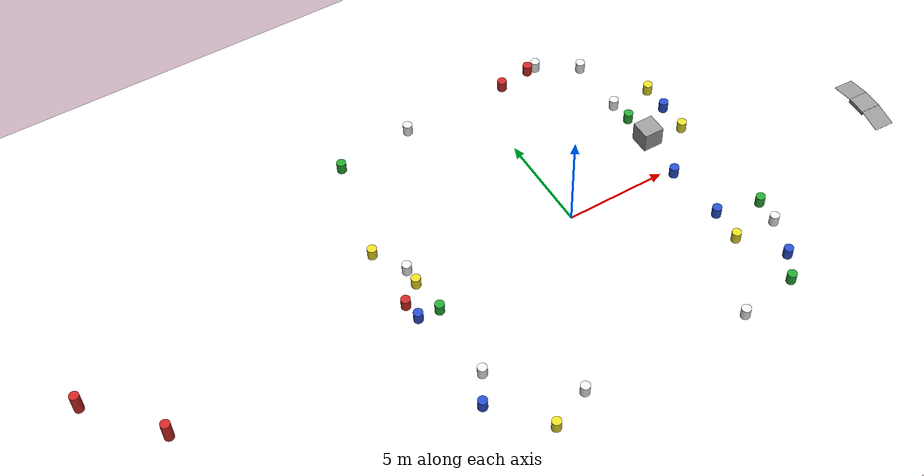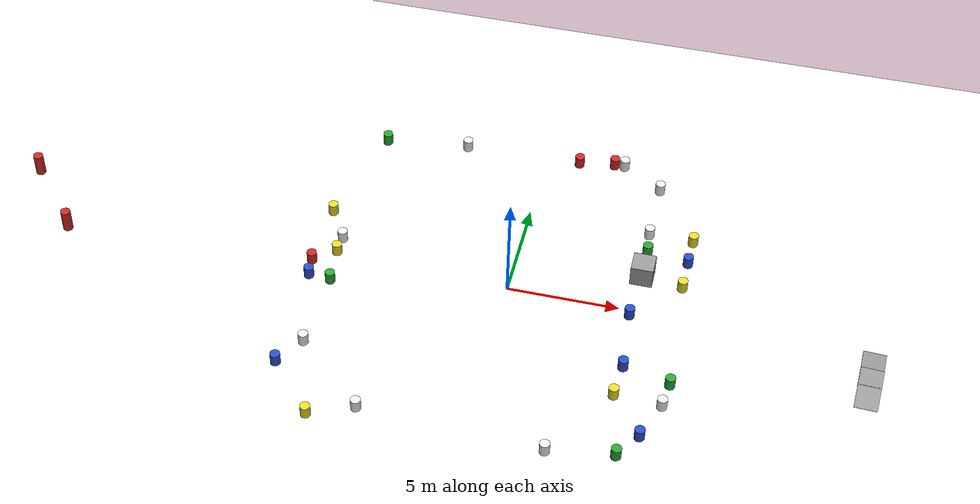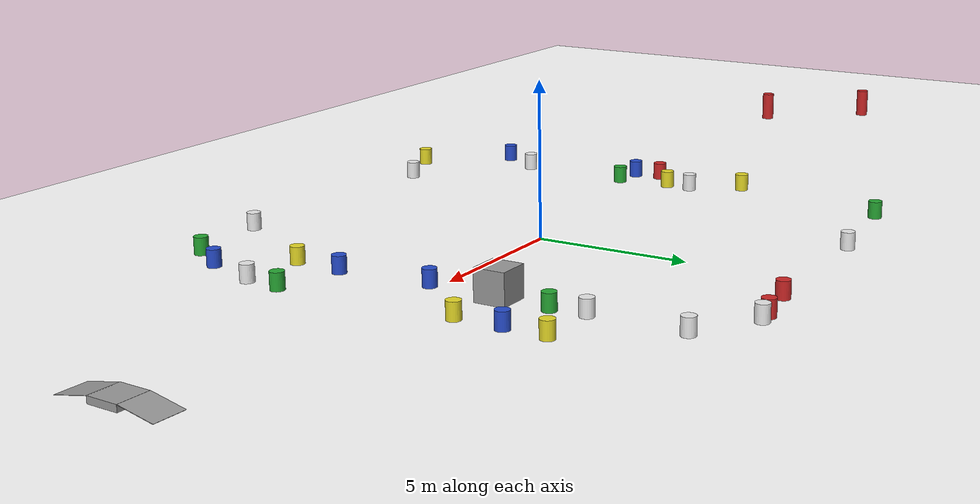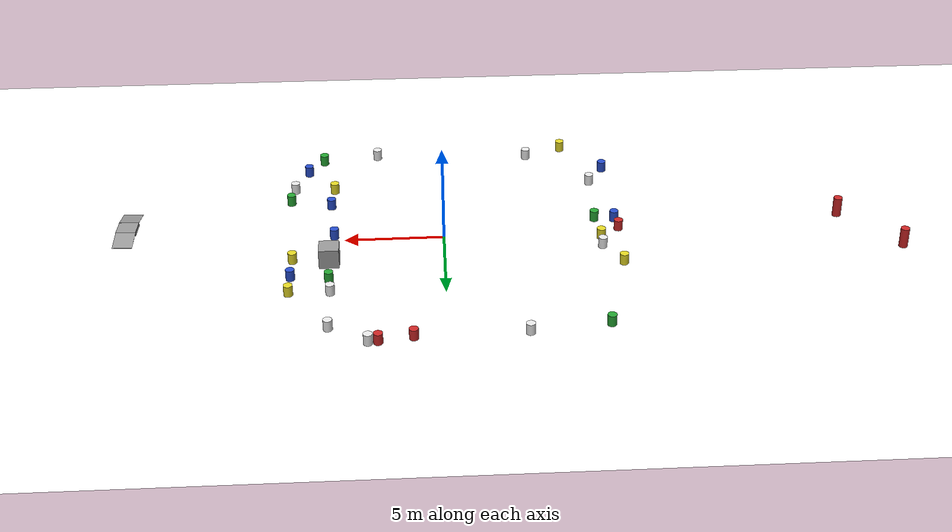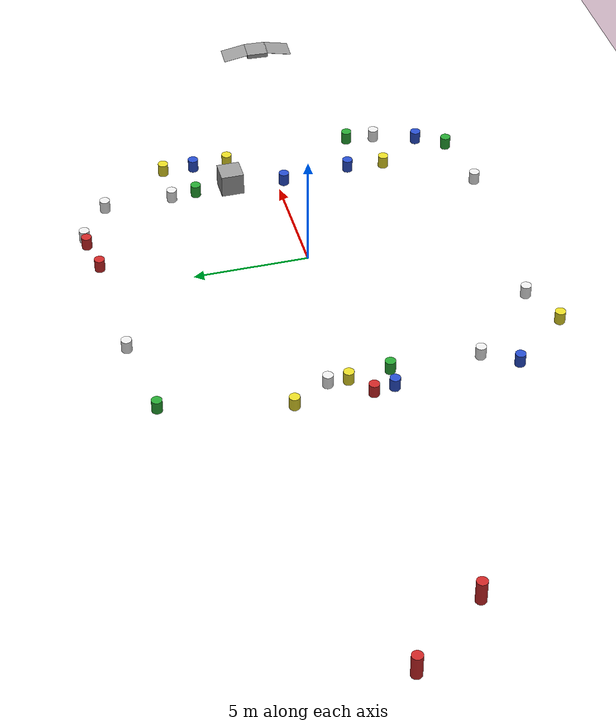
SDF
<sdf version="1.7">
 <world name="IGVC_AutoNav">
  <plugin name="gz::sim::systems::Physics" filename="gz-sim-physics-system"/>
  <plugin name="gz::sim::systems::UserCommands" filename="gz-sim-user-commands-system"/>
  <plugin name="gz::sim::systems::SceneBroadcaster" filename="gz-sim-scene-broadcaster-system"/>
  <plugin name="gz::sim::systems::Contact" filename="gz-sim-contact-system"/>
  <plugin filename="gz-sim-navsat-system" name="gz::sim::systems::NavSat"/>
  <spherical_coordinates>
   <surface_model>EARTH_WGS84</surface_model>
   <world_frame_orientation>ENU</world_frame_orientation>
   <latitude_deg>47.478950</latitude_deg>
   <longitude_deg>19.057785</longitude_deg>
   <elevation>0</elevation>
   <heading_deg>0</heading_deg>
  </spherical_coordinates>
  <plugin name="gz::sim::systems::Sensors" filename="gz-sim-sensors-system">
   <render_engine>ogre2</render_engine>
  </plugin>
  <plugin name="gz::sim::systems::Imu" filename="gz-sim-imu-system"/>
  <plugin name="gz::sim::systems::NavSat" filename="gz-sim-navsat-system"/>
  <light name="sun" type="directional">
   <pose>0 0 10 0 -0 0</pose>
   <diffuse>0.8 0.8 0.8 1</diffuse>
   <specular>0.2 0.2 0.2 1</specular>
   <attenuation>
    <range>1000</range>
    <constant>0.9</constant>
    <linear>0.01</linear>
    <quadratic>0.001</quadratic>
   </attenuation>
   <direction>-0.5 0.1 -0.9</direction>
   <spot><inner_angle>0</inner_angle><outer_angle>0</outer_angle><falloff>0</falloff></spot>
  </light>
  <model name="asphault_ground_plane">
   <static>1</static>
   <link name="link">
    <collision name="collision">
     <geometry><plane><normal>0 0 1</normal><size>64.749 67.342</size></plane></geometry>
     <surface><friction><ode><mu>100</mu><mu2>50</mu2></ode></friction></surface>
    </collision>
    <visual name="visual">
     <cast_shadows>0</cast_shadows>
     <geometry><plane><normal>0 0 1</normal><size>64.749 67.342</size></plane></geometry>
     <material>
      <diffuse>1.0 1.0 1.0</diffuse>
      <specular>1.0 1.0 1.0</specular>
      <pbr><metal><albedo_map>file://media/materials/textures/asphault_v_with_pothole.png</albedo_map></metal></pbr>
     </material>
    </visual>
   </link>
  </model>
  <gravity>0 0 -9.8</gravity>
  <magnetic_field>6e-06 2.3e-05 -4.2e-05</magnetic_field>
  <atmosphere type="adiabatic"/>
  <physics type="ode">
   <max_step_size>0.005</max_step_size>
   <real_time_factor>1</real_time_factor>
   <real_time_update_rate>200</real_time_update_rate>
  </physics>
  <scene><ambient>0.1 0.1 0.1 1</ambient><background>0.0 0.0 0.0 1</background><shadows>1</shadows></scene>
  <spherical_coordinates>
   <surface_model>EARTH_WGS84</surface_model>
   <latitude_deg>0</latitude_deg>
   <longitude_deg>0</longitude_deg>
   <elevation>0</elevation>
   <heading_deg>0</heading_deg>
  </spherical_coordinates>
  <model name="barrel">
   <link name="link">
    <inertial>
     <mass>1</mass>
     <inertia><ixx>0.145833</ixx><ixy>0</ixy><ixz>0</ixz><iyy>0.145833</iyy><iyz>0</iyz><izz>0.125</izz></inertia>
    </inertial>
    <visual name="visual">
     <geometry><cylinder><radius>0.222916</radius><length>1.03567</length></cylinder></geometry>
     <material>
      <script><name>Gazebo/Blue</name><uri>file://media/materials/scripts/gazebo.material</uri></script>
      <shader type="pixel"/>
     </material>
    </visual>
    <collision name="collision">
     <geometry><cylinder><radius>0.222916</radius><length>1.03567</length></cylinder></geometry>
     <surface>
      <friction>
       <ode><mu>1</mu><mu2>1</mu2><fdir1>0 0 0</fdir1><slip1>0</slip1><slip2>0</slip2></ode>
       <torsional>
        <coefficient>1</coefficient>
        <patch_radius>0</patch_radius>
        <surface_radius>0</surface_radius>
        <use_patch_radius>1</use_patch_radius>
        <ode><slip>0</slip></ode>
       </torsional>
      </friction>
      <bounce><restitution_coefficient>0</restitution_coefficient><threshold>1e+06</threshold></bounce>
      <contact>
       <collide_without_contact>0</collide_without_contact>
       <collide_without_contact_bitmask>1</collide_without_contact_bitmask>
       <collide_bitmask>1</collide_bitmask>
       <ode>
        <soft_cfm>0</soft_cfm>
        <soft_erp>0.2</soft_erp>
        <kp>1e+13</kp>
        <kd>1</kd>
        <max_vel>0.01</max_vel>
        <min_depth>0</min_depth>
       </ode>
       <bullet>
        <split_impulse>1</split_impulse>
        <split_impulse_penetration_threshold>-0.01</split_impulse_penetration_threshold>
        <soft_cfm>0</soft_cfm>
        <soft_erp>0.2</soft_erp>
        <kp>1e+13</kp>
        <kd>1</kd>
       </bullet>
      </contact>
     </surface>
    </collision>
   </link>
   <static>0</static>
   <pose>7.06515 -6.91983 0 0 -0 0</pose>
  </model>
  <model name="barrel_0">
   <link name="link">
    <inertial>
     <mass>1</mass>
     <inertia><ixx>0.145833</ixx><ixy>0</ixy><ixz>0</ixz><iyy>0.145833</iyy><iyz>0</iyz><izz>0.125</izz></inertia>
    </inertial>
    <visual name="visual">
     <geometry><cylinder><radius>0.222916</radius><length>1.03567</length></cylinder></geometry>
     <material>
      <script><name>Gazebo/Green</name><uri>file://media/materials/scripts/gazebo.material</uri></script>
      <shader type="pixel"/>
     </material>
    </visual>
    <collision name="collision">
     <geometry><cylinder><radius>0.222916</radius><length>1.03567</length></cylinder></geometry>
     <surface>
      <friction>
       <ode><mu>1</mu><mu2>1</mu2><fdir1>0 0 0</fdir1><slip1>0</slip1><slip2>0</slip2></ode>
       <torsional>
        <coefficient>1</coefficient>
        <patch_radius>0</patch_radius>
        <surface_radius>0</surface_radius>
        <use_patch_radius>1</use_patch_radius>
        <ode><slip>0</slip></ode>
       </torsional>
      </friction>
      <bounce><restitution_coefficient>0</restitution_coefficient><threshold>1e+06</threshold></bounce>
      <contact>
       <collide_without_contact>0</collide_without_contact>
       <collide_without_contact_bitmask>1</collide_without_contact_bitmask>
       <collide_bitmask>1</collide_bitmask>
       <ode>
        <soft_cfm>0</soft_cfm>
        <soft_erp>0.2</soft_erp>
        <kp>1e+13</kp>
        <kd>1</kd>
        <max_vel>0.01</max_vel>
        <min_depth>0</min_depth>
       </ode>
       <bullet>
        <split_impulse>1</split_impulse>
        <split_impulse_penetration_threshold>-0.01</split_impulse_penetration_threshold>
        <soft_cfm>0</soft_cfm>
        <soft_erp>0.2</soft_erp>
        <kp>1e+13</kp>
        <kd>1</kd>
       </bullet>
      </contact>
     </surface>
    </collision>
   </link>
   <static>0</static>
   <pose>6.29971 -8.12332 0 0 -0 0</pose>
  </model>
  <model name="barrel_3">
   <link name="link">
    <inertial>
     <mass>1</mass>
     <inertia><ixx>0.145833</ixx><ixy>0</ixy><ixz>0</ixz><iyy>0.145833</iyy><iyz>0</iyz><izz>0.125</izz></inertia>
    </inertial>
    <visual name="visual">
     <geometry><cylinder><radius>0.222916</radius><length>1.03567</length></cylinder></geometry>
     <material>
      <script><name>Gazebo/White</name><uri>file://media/materials/scripts/gazebo.material</uri></script>
      <shader type="pixel"/>
     </material>
    </visual>
    <collision name="collision">
     <geometry><cylinder><radius>0.222916</radius><length>1.03567</length></cylinder></geometry>
     <surface>
      <friction>
       <ode><mu>1</mu><mu2>1</mu2><fdir1>0 0 0</fdir1><slip1>0</slip1><slip2>0</slip2></ode>
       <torsional>
        <coefficient>1</coefficient>
        <patch_radius>0</patch_radius>
        <surface_radius>0</surface_radius>
        <use_patch_radius>1</use_patch_radius>
        <ode><slip>0</slip></ode>
       </torsional>
      </friction>
      <bounce><restitution_coefficient>0</restitution_coefficient><threshold>1e+06</threshold></bounce>
      <contact>
       <collide_without_contact>0</collide_without_contact>
       <collide_without_contact_bitmask>1</collide_without_contact_bitmask>
       <collide_bitmask>1</collide_bitmask>
       <ode>
        <soft_cfm>0</soft_cfm>
        <soft_erp>0.2</soft_erp>
        <kp>1e+13</kp>
        <kd>1</kd>
        <max_vel>0.01</max_vel>
        <min_depth>0</min_depth>
       </ode>
       <bullet>
        <split_impulse>1</split_impulse>
        <split_impulse_penetration_threshold>-0.01</split_impulse_penetration_threshold>
        <soft_cfm>0</soft_cfm>
        <soft_erp>0.2</soft_erp>
        <kp>1e+13</kp>
        <kd>1</kd>
       </bullet>
      </contact>
     </surface>
    </collision>
   </link>
   <static>0</static>
   <pose>3.42304 -8.56848 0 0 -0 0</pose>
  </model>
  <model name="barrel_4">
   <link name="link">
    <inertial>
     <mass>1</mass>
     <inertia><ixx>0.145833</ixx><ixy>0</ixy><ixz>0</ixz><iyy>0.145833</iyy><iyz>0</iyz><izz>0.125</izz></inertia>
    </inertial>
    <visual name="visual">
     <geometry><cylinder><radius>0.222916</radius><length>1.03567</length></cylinder></geometry>
     <material>
      <script><name>Gazebo/White</name><uri>file://media/materials/scripts/gazebo.material</uri></script>
      <shader type="pixel"/>
     </material>
    </visual>
    <collision name="collision">
     <geometry><cylinder><radius>0.222916</radius><length>1.03567</length></cylinder></geometry>
     <surface>
      <friction>
       <ode><mu>1</mu><mu2>1</mu2><fdir1>0 0 0</fdir1><slip1>0</slip1><slip2>0</slip2></ode>
       <torsional>
        <coefficient>1</coefficient>
        <patch_radius>0</patch_radius>
        <surface_radius>0</surface_radius>
        <use_patch_radius>1</use_patch_radius>
        <ode><slip>0</slip></ode>
       </torsional>
      </friction>
      <bounce><restitution_coefficient>0</restitution_coefficient><threshold>1e+06</threshold></bounce>
      <contact>
       <collide_without_contact>0</collide_without_contact>
       <collide_without_contact_bitmask>1</collide_without_contact_bitmask>
       <collide_bitmask>1</collide_bitmask>
       <ode>
        <soft_cfm>0</soft_cfm>
        <soft_erp>0.2</soft_erp>
        <kp>1e+13</kp>
        <kd>1</kd>
        <max_vel>0.01</max_vel>
        <min_depth>0</min_depth>
       </ode>
       <bullet>
        <split_impulse>1</split_impulse>
        <split_impulse_penetration_threshold>-0.01</split_impulse_penetration_threshold>
        <soft_cfm>0</soft_cfm>
        <soft_erp>0.2</soft_erp>
        <kp>1e+13</kp>
        <kd>1</kd>
       </bullet>
      </contact>
     </surface>
    </collision>
   </link>
   <static>0</static>
   <pose>-4.68415 -8.17797 0 0 -0 0</pose>
  </model>
  <model name="barrel_5">
   <link name="link">
    <inertial>
     <mass>1</mass>
     <inertia><ixx>0.145833</ixx><ixy>0</ixy><ixz>0</ixz><iyy>0.145833</iyy><iyz>0</iyz><izz>0.125</izz></inertia>
    </inertial>
    <visual name="visual">
     <geometry><cylinder><radius>0.222916</radius><length>1.03567</length></cylinder></geometry>
     <material>
      <script><name>Gazebo/Yellow</name><uri>file://media/materials/scripts/gazebo.material</uri></script>
      <shader type="pixel"/>
     </material>
    </visual>
    <collision name="collision">
     <geometry><cylinder><radius>0.222916</radius><length>1.03567</length></cylinder></geometry>
     <surface>
      <friction>
       <ode><mu>1</mu><mu2>1</mu2><fdir1>0 0 0</fdir1><slip1>0</slip1><slip2>0</slip2></ode>
       <torsional>
        <coefficient>1</coefficient>
        <patch_radius>0</patch_radius>
        <surface_radius>0</surface_radius>
        <use_patch_radius>1</use_patch_radius>
        <ode><slip>0</slip></ode>
       </torsional>
      </friction>
      <bounce><restitution_coefficient>0</restitution_coefficient><threshold>1e+06</threshold></bounce>
      <contact>
       <collide_without_contact>0</collide_without_contact>
       <collide_without_contact_bitmask>1</collide_without_contact_bitmask>
       <collide_bitmask>1</collide_bitmask>
       <ode>
        <soft_cfm>0</soft_cfm>
        <soft_erp>0.2</soft_erp>
        <kp>1e+13</kp>
        <kd>1</kd>
        <max_vel>0.01</max_vel>
        <min_depth>0</min_depth>
       </ode>
       <bullet>
        <split_impulse>1</split_impulse>
        <split_impulse_penetration_threshold>-0.01</split_impulse_penetration_threshold>
        <soft_cfm>0</soft_cfm>
        <soft_erp>0.2</soft_erp>
        <kp>1e+13</kp>
        <kd>1</kd>
       </bullet>
      </contact>
     </surface>
    </collision>
   </link>
   <static>0</static>
   <pose>-6.6261 -8.99166 0 0 -0 0</pose>
  </model>
  <model name="barrel_7">
   <link name="link">
    <inertial>
     <mass>1</mass>
     <inertia><ixx>0.145833</ixx><ixy>0</ixy><ixz>0</ixz><iyy>0.145833</iyy><iyz>0</iyz><izz>0.125</izz></inertia>
    </inertial>
    <visual name="visual">
     <geometry><cylinder><radius>0.222916</radius><length>1.03567</length></cylinder></geometry>
     <material>
      <script><name>Gazebo/Blue</name><uri>file://media/materials/scripts/gazebo.material</uri></script>
      <shader type="pixel"/>
     </material>
    </visual>
    <collision name="collision">
     <geometry><cylinder><radius>0.222916</radius><length>1.03567</length></cylinder></geometry>
     <surface>
      <friction>
       <ode><mu>1</mu><mu2>1</mu2><fdir1>0 0 0</fdir1><slip1>0</slip1><slip2>0</slip2></ode>
       <torsional>
        <coefficient>1</coefficient>
        <patch_radius>0</patch_radius>
        <surface_radius>0</surface_radius>
        <use_patch_radius>1</use_patch_radius>
        <ode><slip>0</slip></ode>
       </torsional>
      </friction>
      <bounce><restitution_coefficient>0</restitution_coefficient><threshold>1e+06</threshold></bounce>
      <contact>
       <collide_without_contact>0</collide_without_contact>
       <collide_without_contact_bitmask>1</collide_without_contact_bitmask>
       <collide_bitmask>1</collide_bitmask>
       <ode>
        <soft_cfm>0</soft_cfm>
        <soft_erp>0.2</soft_erp>
        <kp>1e+13</kp>
        <kd>1</kd>
        <max_vel>0.01</max_vel>
        <min_depth>0</min_depth>
       </ode>
       <bullet>
        <split_impulse>1</split_impulse>
        <split_impulse_penetration_threshold>-0.01</split_impulse_penetration_threshold>
        <soft_cfm>0</soft_cfm>
        <soft_erp>0.2</soft_erp>
        <kp>1e+13</kp>
        <kd>1</kd>
       </bullet>
      </contact>
     </surface>
    </collision>
   </link>
   <static>0</static>
   <pose>-8.69384 -6.54838 0 0 -0 0</pose>
  </model>
  <model name="barrel_8">
   <link name="link">
    <inertial>
     <mass>1</mass>
     <inertia><ixx>0.145833</ixx><ixy>0</ixy><ixz>0</ixz><iyy>0.145833</iyy><iyz>0</iyz><izz>0.125</izz></inertia>
    </inertial>
    <visual name="visual">
     <geometry><cylinder><radius>0.222916</radius><length>1.03567</length></cylinder></geometry>
     <material>
      <script><name>Gazebo/White</name><uri>file://media/materials/scripts/gazebo.material</uri></script>
      <shader type="pixel"/>
     </material>
    </visual>
    <collision name="collision">
     <geometry><cylinder><radius>0.222916</radius><length>1.03567</length></cylinder></geometry>
     <surface>
      <friction>
       <ode><mu>1</mu><mu2>1</mu2><fdir1>0 0 0</fdir1><slip1>0</slip1><slip2>0</slip2></ode>
       <torsional>
        <coefficient>1</coefficient>
        <patch_radius>0</patch_radius>
        <surface_radius>0</surface_radius>
        <use_patch_radius>1</use_patch_radius>
        <ode><slip>0</slip></ode>
       </torsional>
      </friction>
      <bounce><restitution_coefficient>0</restitution_coefficient><threshold>1e+06</threshold></bounce>
      <contact>
       <collide_without_contact>0</collide_without_contact>
       <collide_without_contact_bitmask>1</collide_without_contact_bitmask>
       <collide_bitmask>1</collide_bitmask>
       <ode>
        <soft_cfm>0</soft_cfm>
        <soft_erp>0.2</soft_erp>
        <kp>1e+13</kp>
        <kd>1</kd>
        <max_vel>0.01</max_vel>
        <min_depth>0</min_depth>
       </ode>
       <bullet>
        <split_impulse>1</split_impulse>
        <split_impulse_penetration_threshold>-0.01</split_impulse_penetration_threshold>
        <soft_cfm>0</soft_cfm>
        <soft_erp>0.2</soft_erp>
        <kp>1e+13</kp>
        <kd>1</kd>
       </bullet>
      </contact>
     </surface>
    </collision>
   </link>
   <static>0</static>
   <pose>-7.87307 -5.14972 0 0 -0 0</pose>
  </model>
  <model name="barrel_10">
   <link name="link">
    <inertial>
     <mass>1</mass>
     <inertia><ixx>0.145833</ixx><ixy>0</ixy><ixz>0</ixz><iyy>0.145833</iyy><iyz>0</iyz><izz>0.125</izz></inertia>
    </inertial>
    <visual name="visual">
     <geometry><cylinder><radius>0.222916</radius><length>1.03567</length></cylinder></geometry>
     <material>
      <script><name>Gazebo/Blue</name><uri>file://media/materials/scripts/gazebo.material</uri></script>
      <shader type="pixel"/>
     </material>
    </visual>
    <collision name="collision">
     <geometry><cylinder><radius>0.222916</radius><length>1.03567</length></cylinder></geometry>
     <surface>
      <friction>
       <ode><mu>1</mu><mu2>1</mu2><fdir1>0 0 0</fdir1><slip1>0</slip1><slip2>0</slip2></ode>
       <torsional>
        <coefficient>1</coefficient>
        <patch_radius>0</patch_radius>
        <surface_radius>0</surface_radius>
        <use_patch_radius>1</use_patch_radius>
        <ode><slip>0</slip></ode>
       </torsional>
      </friction>
      <bounce><restitution_coefficient>0</restitution_coefficient><threshold>1e+06</threshold></bounce>
      <contact>
       <collide_without_contact>0</collide_without_contact>
       <collide_without_contact_bitmask>1</collide_without_contact_bitmask>
       <collide_bitmask>1</collide_bitmask>
       <ode>
        <soft_cfm>0</soft_cfm>
        <soft_erp>0.2</soft_erp>
        <kp>1e+13</kp>
        <kd>1</kd>
        <max_vel>0.01</max_vel>
        <min_depth>0</min_depth>
       </ode>
       <bullet>
        <split_impulse>1</split_impulse>
        <split_impulse_penetration_threshold>-0.01</split_impulse_penetration_threshold>
        <soft_cfm>0</soft_cfm>
        <soft_erp>0.2</soft_erp>
        <kp>1e+13</kp>
        <kd>1</kd>
       </bullet>
      </contact>
     </surface>
    </collision>
   </link>
   <static>0</static>
   <pose>-8.77961 -1.26823 0 0 -0 0</pose>
  </model>
  <model name="barrel_11">
   <link name="link">
    <inertial>
     <mass>1</mass>
     <inertia><ixx>0.145833</ixx><ixy>0</ixy><ixz>0</ixz><iyy>0.145833</iyy><iyz>0</iyz><izz>0.125</izz></inertia>
    </inertial>
    <visual name="visual">
     <geometry><cylinder><radius>0.222916</radius><length>1.03567</length></cylinder></geometry>
     <material>
      <script><name>Gazebo/Yellow</name><uri>file://media/materials/scripts/gazebo.material</uri></script>
      <shader type="pixel"/>
     </material>
    </visual>
    <collision name="collision">
     <geometry><cylinder><radius>0.222916</radius><length>1.03567</length></cylinder></geometry>
     <surface>
      <friction>
       <ode><mu>1</mu><mu2>1</mu2><fdir1>0 0 0</fdir1><slip1>0</slip1><slip2>0</slip2></ode>
       <torsional>
        <coefficient>1</coefficient>
        <patch_radius>0</patch_radius>
        <surface_radius>0</surface_radius>
        <use_patch_radius>1</use_patch_radius>
        <ode><slip>0</slip></ode>
       </torsional>
      </friction>
      <bounce><restitution_coefficient>0</restitution_coefficient><threshold>1e+06</threshold></bounce>
      <contact>
       <collide_without_contact>0</collide_without_contact>
       <collide_without_contact_bitmask>1</collide_without_contact_bitmask>
       <collide_bitmask>1</collide_bitmask>
       <ode>
        <soft_cfm>0</soft_cfm>
        <soft_erp>0.2</soft_erp>
        <kp>1e+13</kp>
        <kd>1</kd>
        <max_vel>0.01</max_vel>
        <min_depth>0</min_depth>
       </ode>
       <bullet>
        <split_impulse>1</split_impulse>
        <split_impulse_penetration_threshold>-0.01</split_impulse_penetration_threshold>
        <soft_cfm>0</soft_cfm>
        <soft_erp>0.2</soft_erp>
        <kp>1e+13</kp>
        <kd>1</kd>
       </bullet>
      </contact>
     </surface>
    </collision>
   </link>
   <static>0</static>
   <pose>-7.95424 0.411738 0 0 -0 0</pose>
  </model>
  <model name="barrel_13">
   <link name="link">
    <inertial>
     <mass>1</mass>
     <inertia><ixx>0.145833</ixx><ixy>0</ixy><ixz>0</ixz><iyy>0.145833</iyy><iyz>0</iyz><izz>0.125</izz></inertia>
    </inertial>
    <visual name="visual">
     <geometry><cylinder><radius>0.222916</radius><length>1.03567</length></cylinder></geometry>
     <material>
      <script><name>Gazebo/Green</name><uri>file://media/materials/scripts/gazebo.material</uri></script>
      <shader type="pixel"/>
     </material>
    </visual>
    <collision name="collision">
     <geometry><cylinder><radius>0.222916</radius><length>1.03567</length></cylinder></geometry>
     <surface>
      <friction>
       <ode><mu>1</mu><mu2>1</mu2><fdir1>0 0 0</fdir1><slip1>0</slip1><slip2>0</slip2></ode>
       <torsional>
        <coefficient>1</coefficient>
        <patch_radius>0</patch_radius>
        <surface_radius>0</surface_radius>
        <use_patch_radius>1</use_patch_radius>
        <ode><slip>0</slip></ode>
       </torsional>
      </friction>
      <bounce><restitution_coefficient>0</restitution_coefficient><threshold>1e+06</threshold></bounce>
      <contact>
       <collide_without_contact>0</collide_without_contact>
       <collide_without_contact_bitmask>1</collide_without_contact_bitmask>
       <collide_bitmask>1</collide_bitmask>
       <ode>
        <soft_cfm>0</soft_cfm>
        <soft_erp>0.2</soft_erp>
        <kp>1e+13</kp>
        <kd>1</kd>
        <max_vel>0.01</max_vel>
        <min_depth>0</min_depth>
       </ode>
       <bullet>
        <split_impulse>1</split_impulse>
        <split_impulse_penetration_threshold>-0.01</split_impulse_penetration_threshold>
        <soft_cfm>0</soft_cfm>
        <soft_erp>0.2</soft_erp>
        <kp>1e+13</kp>
        <kd>1</kd>
       </bullet>
      </contact>
     </surface>
    </collision>
   </link>
   <static>0</static>
   <pose>-7.76944 -1.36844 0 0 -0 0</pose>
  </model>
  <model name="barrel_14">
   <link name="link">
    <inertial>
     <mass>1</mass>
     <inertia><ixx>0.145833</ixx><ixy>0</ixy><ixz>0</ixz><iyy>0.145833</iyy><iyz>0</iyz><izz>0.125</izz></inertia>
    </inertial>
    <visual name="visual">
     <geometry><cylinder><radius>0.222916</radius><length>1.03567</length></cylinder></geometry>
     <material>
      <script><name>Gazebo/Red</name><uri>file://media/materials/scripts/gazebo.material</uri></script>
      <shader type="pixel"/>
     </material>
    </visual>
    <collision name="collision">
     <geometry><cylinder><radius>0.222916</radius><length>1.03567</length></cylinder></geometry>
     <surface>
      <friction>
       <ode><mu>1</mu><mu2>1</mu2><fdir1>0 0 0</fdir1><slip1>0</slip1><slip2>0</slip2></ode>
       <torsional>
        <coefficient>1</coefficient>
        <patch_radius>0</patch_radius>
        <surface_radius>0</surface_radius>
        <use_patch_radius>1</use_patch_radius>
        <ode><slip>0</slip></ode>
       </torsional>
      </friction>
      <bounce><restitution_coefficient>0</restitution_coefficient><threshold>1e+06</threshold></bounce>
      <contact>
       <collide_without_contact>0</collide_without_contact>
       <collide_without_contact_bitmask>1</collide_without_contact_bitmask>
       <collide_bitmask>1</collide_bitmask>
       <ode>
        <soft_cfm>0</soft_cfm>
        <soft_erp>0.2</soft_erp>
        <kp>1e+13</kp>
        <kd>1</kd>
        <max_vel>0.01</max_vel>
        <min_depth>0</min_depth>
       </ode>
       <bullet>
        <split_impulse>1</split_impulse>
        <split_impulse_penetration_threshold>-0.01</split_impulse_penetration_threshold>
        <soft_cfm>0</soft_cfm>
        <soft_erp>0.2</soft_erp>
        <kp>1e+13</kp>
        <kd>1</kd>
       </bullet>
      </contact>
     </surface>
    </collision>
   </link>
   <static>0</static>
   <pose>-8.90413 -0.368182 0 0 -0 0</pose>
  </model>
  <model name="barrel_15">
   <link name="link">
    <inertial>
     <mass>1</mass>
     <inertia><ixx>0.145833</ixx><ixy>0</ixy><ixz>0</ixz><iyy>0.145833</iyy><iyz>0</iyz><izz>0.125</izz></inertia>
    </inertial>
    <visual name="visual">
     <geometry><cylinder><radius>0.222916</radius><length>1.03567</length></cylinder></geometry>
     <material>
      <script><name>Gazebo/White</name><uri>file://media/materials/scripts/gazebo.material</uri></script>
      <shader type="pixel"/>
     </material>
    </visual>
    <collision name="collision">
     <geometry><cylinder><radius>0.222916</radius><length>1.03567</length></cylinder></geometry>
     <surface>
      <friction>
       <ode><mu>1</mu><mu2>1</mu2><fdir1>0 0 0</fdir1><slip1>0</slip1><slip2>0</slip2></ode>
       <torsional>
        <coefficient>1</coefficient>
        <patch_radius>0</patch_radius>
        <surface_radius>0</surface_radius>
        <use_patch_radius>1</use_patch_radius>
        <ode><slip>0</slip></ode>
       </torsional>
      </friction>
      <bounce><restitution_coefficient>0</restitution_coefficient><threshold>1e+06</threshold></bounce>
      <contact>
       <collide_without_contact>0</collide_without_contact>
       <collide_without_contact_bitmask>1</collide_without_contact_bitmask>
       <collide_bitmask>1</collide_bitmask>
       <ode>
        <soft_cfm>0</soft_cfm>
        <soft_erp>0.2</soft_erp>
        <kp>1e+13</kp>
        <kd>1</kd>
        <max_vel>0.01</max_vel>
        <min_depth>0</min_depth>
       </ode>
       <bullet>
        <split_impulse>1</split_impulse>
        <split_impulse_penetration_threshold>-0.01</split_impulse_penetration_threshold>
        <soft_cfm>0</soft_cfm>
        <soft_erp>0.2</soft_erp>
        <kp>1e+13</kp>
        <kd>1</kd>
       </bullet>
      </contact>
     </surface>
    </collision>
   </link>
   <static>0</static>
   <pose>-7.93751 1.27262 0 0 -0 0</pose>
  </model>
  <model name="barrel_16">
   <link name="link">
    <inertial>
     <mass>1</mass>
     <inertia><ixx>0.145833</ixx><ixy>0</ixy><ixz>0</ixz><iyy>0.145833</iyy><iyz>0</iyz><izz>0.125</izz></inertia>
    </inertial>
    <visual name="visual">
     <geometry><cylinder><radius>0.222916</radius><length>1.03567</length></cylinder></geometry>
     <material>
      <script><name>Gazebo/Yellow</name><uri>file://media/materials/scripts/gazebo.material</uri></script>
      <shader type="pixel"/>
     </material>
    </visual>
    <collision name="collision">
     <geometry><cylinder><radius>0.222916</radius><length>1.03567</length></cylinder></geometry>
     <surface>
      <friction>
       <ode><mu>1</mu><mu2>1</mu2><fdir1>0 0 0</fdir1><slip1>0</slip1><slip2>0</slip2></ode>
       <torsional>
        <coefficient>1</coefficient>
        <patch_radius>0</patch_radius>
        <surface_radius>0</surface_radius>
        <use_patch_radius>1</use_patch_radius>
        <ode><slip>0</slip></ode>
       </torsional>
      </friction>
      <bounce><restitution_coefficient>0</restitution_coefficient><threshold>1e+06</threshold></bounce>
      <contact>
       <collide_without_contact>0</collide_without_contact>
       <collide_without_contact_bitmask>1</collide_without_contact_bitmask>
       <collide_bitmask>1</collide_bitmask>
       <ode>
        <soft_cfm>0</soft_cfm>
        <soft_erp>0.2</soft_erp>
        <kp>1e+13</kp>
        <kd>1</kd>
        <max_vel>0.01</max_vel>
        <min_depth>0</min_depth>
       </ode>
       <bullet>
        <split_impulse>1</split_impulse>
        <split_impulse_penetration_threshold>-0.01</split_impulse_penetration_threshold>
        <soft_cfm>0</soft_cfm>
        <soft_erp>0.2</soft_erp>
        <kp>1e+13</kp>
        <kd>1</kd>
       </bullet>
      </contact>
     </surface>
    </collision>
   </link>
   <static>0</static>
   <pose>-8.83069 2.86357 0 0 -0 0</pose>
  </model>
  <model name="barrel_22">
   <link name="link">
    <inertial>
     <mass>1</mass>
     <inertia><ixx>0.145833</ixx><ixy>0</ixy><ixz>0</ixz><iyy>0.145833</iyy><iyz>0</iyz><izz>0.125</izz></inertia>
    </inertial>
    <visual name="visual">
     <geometry><cylinder><radius>0.222916</radius><length>1.03567</length></cylinder></geometry>
     <material>
      <script><name>Gazebo/White</name><uri>file://media/materials/scripts/gazebo.material</uri></script>
      <shader type="pixel"/>
     </material>
    </visual>
    <collision name="collision">
     <geometry><cylinder><radius>0.222916</radius><length>1.03567</length></cylinder></geometry>
     <surface>
      <friction>
       <ode><mu>1</mu><mu2>1</mu2><fdir1>0 0 0</fdir1><slip1>0</slip1><slip2>0</slip2></ode>
       <torsional>
        <coefficient>1</coefficient>
        <patch_radius>0</patch_radius>
        <surface_radius>0</surface_radius>
        <use_patch_radius>1</use_patch_radius>
        <ode><slip>0</slip></ode>
       </torsional>
      </friction>
      <bounce><restitution_coefficient>0</restitution_coefficient><threshold>1e+06</threshold></bounce>
      <contact>
       <collide_without_contact>0</collide_without_contact>
       <collide_without_contact_bitmask>1</collide_without_contact_bitmask>
       <collide_bitmask>1</collide_bitmask>
       <ode>
        <soft_cfm>0</soft_cfm>
        <soft_erp>0.2</soft_erp>
        <kp>1e+13</kp>
        <kd>1</kd>
        <max_vel>0.01</max_vel>
        <min_depth>0</min_depth>
       </ode>
       <bullet>
        <split_impulse>1</split_impulse>
        <split_impulse_penetration_threshold>-0.01</split_impulse_penetration_threshold>
        <soft_cfm>0</soft_cfm>
        <soft_erp>0.2</soft_erp>
        <kp>1e+13</kp>
        <kd>1</kd>
       </bullet>
      </contact>
     </surface>
    </collision>
   </link>
   <static>0</static>
   <pose>-3.80549 8.61142 0 0 -0 0</pose>
  </model>
  <model name="barrel_23">
   <link name="link">
    <inertial>
     <mass>1</mass>
     <inertia><ixx>0.145833</ixx><ixy>0</ixy><ixz>0</ixz><iyy>0.145833</iyy><iyz>0</iyz><izz>0.125</izz></inertia>
    </inertial>
    <visual name="visual">
     <geometry><cylinder><radius>0.222916</radius><length>1.03567</length></cylinder></geometry>
     <material>
      <script><name>Gazebo/Green</name><uri>file://media/materials/scripts/gazebo.material</uri></script>
      <shader type="pixel"/>
     </material>
    </visual>
    <collision name="collision">
     <geometry><cylinder><radius>0.222916</radius><length>1.03567</length></cylinder></geometry>
     <surface>
      <friction>
       <ode><mu>1</mu><mu2>1</mu2><fdir1>0 0 0</fdir1><slip1>0</slip1><slip2>0</slip2></ode>
       <torsional>
        <coefficient>1</coefficient>
        <patch_radius>0</patch_radius>
        <surface_radius>0</surface_radius>
        <use_patch_radius>1</use_patch_radius>
        <ode><slip>0</slip></ode>
       </torsional>
      </friction>
      <bounce><restitution_coefficient>0</restitution_coefficient><threshold>1e+06</threshold></bounce>
      <contact>
       <collide_without_contact>0</collide_without_contact>
       <collide_without_contact_bitmask>1</collide_without_contact_bitmask>
       <collide_bitmask>1</collide_bitmask>
       <ode>
        <soft_cfm>0</soft_cfm>
        <soft_erp>0.2</soft_erp>
        <kp>1e+13</kp>
        <kd>1</kd>
        <max_vel>0.01</max_vel>
        <min_depth>0</min_depth>
       </ode>
       <bullet>
        <split_impulse>1</split_impulse>
        <split_impulse_penetration_threshold>-0.01</split_impulse_penetration_threshold>
        <soft_cfm>0</soft_cfm>
        <soft_erp>0.2</soft_erp>
        <kp>1e+13</kp>
        <kd>1</kd>
       </bullet>
      </contact>
     </surface>
    </collision>
   </link>
   <static>0</static>
   <pose>-7.63083 8.13447 0 0 -0 0</pose>
  </model>
  <model name="barrel_24">
   <link name="link">
    <inertial>
     <mass>1</mass>
     <inertia><ixx>0.145833</ixx><ixy>0</ixy><ixz>0</ixz><iyy>0.145833</iyy><iyz>0</iyz><izz>0.125</izz></inertia>
    </inertial>
    <visual name="visual">
     <geometry><cylinder><radius>0.222916</radius><length>1.03567</length></cylinder></geometry>
     <material>
      <script><name>Gazebo/White</name><uri>file://media/materials/scripts/gazebo.material</uri></script>
      <shader type="pixel"/>
     </material>
    </visual>
    <collision name="collision">
     <geometry><cylinder><radius>0.222916</radius><length>1.03567</length></cylinder></geometry>
     <surface>
      <friction>
       <ode><mu>1</mu><mu2>1</mu2><fdir1>0 0 0</fdir1><slip1>0</slip1><slip2>0</slip2></ode>
       <torsional>
        <coefficient>1</coefficient>
        <patch_radius>0</patch_radius>
        <surface_radius>0</surface_radius>
        <use_patch_radius>1</use_patch_radius>
        <ode><slip>0</slip></ode>
       </torsional>
      </friction>
      <bounce><restitution_coefficient>0</restitution_coefficient><threshold>1e+06</threshold></bounce>
      <contact>
       <collide_without_contact>0</collide_without_contact>
       <collide_without_contact_bitmask>1</collide_without_contact_bitmask>
       <collide_bitmask>1</collide_bitmask>
       <ode>
        <soft_cfm>0</soft_cfm>
        <soft_erp>0.2</soft_erp>
        <kp>1e+13</kp>
        <kd>1</kd>
        <max_vel>0.01</max_vel>
        <min_depth>0</min_depth>
       </ode>
       <bullet>
        <split_impulse>1</split_impulse>
        <split_impulse_penetration_threshold>-0.01</split_impulse_penetration_threshold>
        <soft_cfm>0</soft_cfm>
        <soft_erp>0.2</soft_erp>
        <kp>1e+13</kp>
        <kd>1</kd>
       </bullet>
      </contact>
     </surface>
    </collision>
   </link>
   <static>0</static>
   <pose>5.56898 7.78097 0 0 -0 0</pose>
  </model>
  <model name="barrel_26">
   <link name="link">
    <inertial>
     <mass>1</mass>
     <inertia><ixx>0.145833</ixx><ixy>0</ixy><ixz>0</ixz><iyy>0.145833</iyy><iyz>0</iyz><izz>0.125</izz></inertia>
    </inertial>
    <visual name="visual">
     <geometry><cylinder><radius>0.222916</radius><length>1.03567</length></cylinder></geometry>
     <material>
      <script><name>Gazebo/Red</name><uri>file://media/materials/scripts/gazebo.material</uri></script>
      <shader type="pixel"/>
     </material>
    </visual>
    <collision name="collision">
     <geometry><cylinder><radius>0.222916</radius><length>1.03567</length></cylinder></geometry>
     <surface>
      <friction>
       <ode><mu>1</mu><mu2>1</mu2><fdir1>0 0 0</fdir1><slip1>0</slip1><slip2>0</slip2></ode>
       <torsional>
        <coefficient>1</coefficient>
        <patch_radius>0</patch_radius>
        <surface_radius>0</surface_radius>
        <use_patch_radius>1</use_patch_radius>
        <ode><slip>0</slip></ode>
       </torsional>
      </friction>
      <bounce><restitution_coefficient>0</restitution_coefficient><threshold>1e+06</threshold></bounce>
      <contact>
       <collide_without_contact>0</collide_without_contact>
       <collide_without_contact_bitmask>1</collide_without_contact_bitmask>
       <collide_bitmask>1</collide_bitmask>
       <ode>
        <soft_cfm>0</soft_cfm>
        <soft_erp>0.2</soft_erp>
        <kp>1e+13</kp>
        <kd>1</kd>
        <max_vel>0.01</max_vel>
        <min_depth>0</min_depth>
       </ode>
       <bullet>
        <split_impulse>1</split_impulse>
        <split_impulse_penetration_threshold>-0.01</split_impulse_penetration_threshold>
        <soft_cfm>0</soft_cfm>
        <soft_erp>0.2</soft_erp>
        <kp>1e+13</kp>
        <kd>1</kd>
       </bullet>
      </contact>
     </surface>
    </collision>
   </link>
   <static>0</static>
   <pose>1.5857 8.73654 0 0 -0 0</pose>
  </model>
  <model name="barrel_27">
   <link name="link">
    <inertial>
     <mass>1</mass>
     <inertia><ixx>0.145833</ixx><ixy>0</ixy><ixz>0</ixz><iyy>0.145833</iyy><iyz>0</iyz><izz>0.125</izz></inertia>
    </inertial>
    <visual name="visual">
     <geometry><cylinder><radius>0.222916</radius><length>1.03567</length></cylinder></geometry>
     <material>
      <script><name>Gazebo/Red</name><uri>file://media/materials/scripts/gazebo.material</uri></script>
      <shader type="pixel"/>
     </material>
    </visual>
    <collision name="collision">
     <geometry><cylinder><radius>0.222916</radius><length>1.03567</length></cylinder></geometry>
     <surface>
      <friction>
       <ode><mu>1</mu><mu2>1</mu2><fdir1>0 0 0</fdir1><slip1>0</slip1><slip2>0</slip2></ode>
       <torsional>
        <coefficient>1</coefficient>
        <patch_radius>0</patch_radius>
        <surface_radius>0</surface_radius>
        <use_patch_radius>1</use_patch_radius>
        <ode><slip>0</slip></ode>
       </torsional>
      </friction>
      <bounce><restitution_coefficient>0</restitution_coefficient><threshold>1e+06</threshold></bounce>
      <contact>
       <collide_without_contact>0</collide_without_contact>
       <collide_without_contact_bitmask>1</collide_without_contact_bitmask>
       <collide_bitmask>1</collide_bitmask>
       <ode>
        <soft_cfm>0</soft_cfm>
        <soft_erp>0.2</soft_erp>
        <kp>1e+13</kp>
        <kd>1</kd>
        <max_vel>0.01</max_vel>
        <min_depth>0</min_depth>
       </ode>
       <bullet>
        <split_impulse>1</split_impulse>
        <split_impulse_penetration_threshold>-0.01</split_impulse_penetration_threshold>
        <soft_cfm>0</soft_cfm>
        <soft_erp>0.2</soft_erp>
        <kp>1e+13</kp>
        <kd>1</kd>
       </bullet>
      </contact>
     </surface>
    </collision>
   </link>
   <static>0</static>
   <pose>3.2217 9.00431 0 0 -0 0</pose>
  </model>
  <model name="barrel_28">
   <link name="link">
    <inertial>
     <mass>1</mass>
     <inertia><ixx>0.145833</ixx><ixy>0</ixy><ixz>0</ixz><iyy>0.145833</iyy><iyz>0</iyz><izz>0.125</izz></inertia>
    </inertial>
    <visual name="visual">
     <geometry><cylinder><radius>0.222916</radius><length>1.03567</length></cylinder></geometry>
     <material>
      <script><name>Gazebo/White</name><uri>file://media/materials/scripts/gazebo.material</uri></script>
      <shader type="pixel"/>
     </material>
    </visual>
    <collision name="collision">
     <geometry><cylinder><radius>0.222916</radius><length>1.03567</length></cylinder></geometry>
     <surface>
      <friction>
       <ode><mu>1</mu><mu2>1</mu2><fdir1>0 0 0</fdir1><slip1>0</slip1><slip2>0</slip2></ode>
       <torsional>
        <coefficient>1</coefficient>
        <patch_radius>0</patch_radius>
        <surface_radius>0</surface_radius>
        <use_patch_radius>1</use_patch_radius>
        <ode><slip>0</slip></ode>
       </torsional>
      </friction>
      <bounce><restitution_coefficient>0</restitution_coefficient><threshold>1e+06</threshold></bounce>
      <contact>
       <collide_without_contact>0</collide_without_contact>
       <collide_without_contact_bitmask>1</collide_without_contact_bitmask>
       <collide_bitmask>1</collide_bitmask>
       <ode>
        <soft_cfm>0</soft_cfm>
        <soft_erp>0.2</soft_erp>
        <kp>1e+13</kp>
        <kd>1</kd>
        <max_vel>0.01</max_vel>
        <min_depth>0</min_depth>
       </ode>
       <bullet>
        <split_impulse>1</split_impulse>
        <split_impulse_penetration_threshold>-0.01</split_impulse_penetration_threshold>
        <soft_cfm>0</soft_cfm>
        <soft_erp>0.2</soft_erp>
        <kp>1e+13</kp>
        <kd>1</kd>
       </bullet>
      </contact>
     </surface>
    </collision>
   </link>
   <static>0</static>
   <pose>3.68913 9.02449 0 0 -0 0</pose>
  </model>
  <model name="barrel_30">
   <link name="link">
    <inertial>
     <mass>1</mass>
     <inertia><ixx>0.145833</ixx><ixy>0</ixy><ixz>0</ixz><iyy>0.145833</iyy><iyz>0</iyz><izz>0.125</izz></inertia>
    </inertial>
    <visual name="visual">
     <geometry><cylinder><radius>0.222916</radius><length>1.03567</length></cylinder></geometry>
     <material>
      <script><name>Gazebo/Green</name><uri>file://media/materials/scripts/gazebo.material</uri></script>
      <shader type="pixel"/>
     </material>
    </visual>
    <collision name="collision">
     <geometry><cylinder><radius>0.222916</radius><length>1.03567</length></cylinder></geometry>
     <surface>
      <friction>
       <ode><mu>1</mu><mu2>1</mu2><fdir1>0 0 0</fdir1><slip1>0</slip1><slip2>0</slip2></ode>
       <torsional>
        <coefficient>1</coefficient>
        <patch_radius>0</patch_radius>
        <surface_radius>0</surface_radius>
        <use_patch_radius>1</use_patch_radius>
        <ode><slip>0</slip></ode>
       </torsional>
      </friction>
      <bounce><restitution_coefficient>0</restitution_coefficient><threshold>1e+06</threshold></bounce>
      <contact>
       <collide_without_contact>0</collide_without_contact>
       <collide_without_contact_bitmask>1</collide_without_contact_bitmask>
       <collide_bitmask>1</collide_bitmask>
       <ode>
        <soft_cfm>0</soft_cfm>
        <soft_erp>0.2</soft_erp>
        <kp>1e+13</kp>
        <kd>1</kd>
        <max_vel>0.01</max_vel>
        <min_depth>0</min_depth>
       </ode>
       <bullet>
        <split_impulse>1</split_impulse>
        <split_impulse_penetration_threshold>-0.01</split_impulse_penetration_threshold>
        <soft_cfm>0</soft_cfm>
        <soft_erp>0.2</soft_erp>
        <kp>1e+13</kp>
        <kd>1</kd>
       </bullet>
      </contact>
     </surface>
    </collision>
   </link>
   <static>0</static>
   <pose>7.85271 -3.86064 0 0 -0 0</pose>
  </model>
  <model name="barrel_31">
   <link name="link">
    <inertial>
     <mass>1</mass>
     <inertia><ixx>0.145833</ixx><ixy>0</ixy><ixz>0</ixz><iyy>0.145833</iyy><iyz>0</iyz><izz>0.125</izz></inertia>
    </inertial>
    <visual name="visual">
     <geometry><cylinder><radius>0.222916</radius><length>1.03567</length></cylinder></geometry>
     <material>
      <script><name>Gazebo/Green</name><uri>file://media/materials/scripts/gazebo.material</uri></script>
      <shader type="pixel"/>
     </material>
    </visual>
    <collision name="collision">
     <geometry><cylinder><radius>0.222916</radius><length>1.03567</length></cylinder></geometry>
     <surface>
      <friction>
       <ode><mu>1</mu><mu2>1</mu2><fdir1>0 0 0</fdir1><slip1>0</slip1><slip2>0</slip2></ode>
       <torsional>
        <coefficient>1</coefficient>
        <patch_radius>0</patch_radius>
        <surface_radius>0</surface_radius>
        <use_patch_radius>1</use_patch_radius>
        <ode><slip>0</slip></ode>
       </torsional>
      </friction>
      <bounce><restitution_coefficient>0</restitution_coefficient><threshold>1e+06</threshold></bounce>
      <contact>
       <collide_without_contact>0</collide_without_contact>
       <collide_without_contact_bitmask>1</collide_without_contact_bitmask>
       <collide_bitmask>1</collide_bitmask>
       <ode>
        <soft_cfm>0</soft_cfm>
        <soft_erp>0.2</soft_erp>
        <kp>1e+13</kp>
        <kd>1</kd>
        <max_vel>0.01</max_vel>
        <min_depth>0</min_depth>
       </ode>
       <bullet>
        <split_impulse>1</split_impulse>
        <split_impulse_penetration_threshold>-0.01</split_impulse_penetration_threshold>
        <soft_cfm>0</soft_cfm>
        <soft_erp>0.2</soft_erp>
        <kp>1e+13</kp>
        <kd>1</kd>
       </bullet>
      </contact>
     </surface>
    </collision>
   </link>
   <static>0</static>
   <pose>5.66048 3.67983 0 0 -0 0</pose>
  </model>
  <model name="barrel_32">
   <link name="link">
    <inertial>
     <mass>1</mass>
     <inertia><ixx>0.145833</ixx><ixy>0</ixy><ixz>0</ixz><iyy>0.145833</iyy><iyz>0</iyz><izz>0.125</izz></inertia>
    </inertial>
    <visual name="visual">
     <geometry><cylinder><radius>0.222916</radius><length>1.03567</length></cylinder></geometry>
     <material>
      <script><name>Gazebo/Yellow</name><uri>file://media/materials/scripts/gazebo.material</uri></script>
      <shader type="pixel"/>
     </material>
    </visual>
    <collision name="collision">
     <geometry><cylinder><radius>0.222916</radius><length>1.03567</length></cylinder></geometry>
     <surface>
      <friction>
       <ode><mu>1</mu><mu2>1</mu2><fdir1>0 0 0</fdir1><slip1>0</slip1><slip2>0</slip2></ode>
       <torsional>
        <coefficient>1</coefficient>
        <patch_radius>0</patch_radius>
        <surface_radius>0</surface_radius>
        <use_patch_radius>1</use_patch_radius>
        <ode><slip>0</slip></ode>
       </torsional>
      </friction>
      <bounce><restitution_coefficient>0</restitution_coefficient><threshold>1e+06</threshold></bounce>
      <contact>
       <collide_without_contact>0</collide_without_contact>
       <collide_without_contact_bitmask>1</collide_without_contact_bitmask>
       <collide_bitmask>1</collide_bitmask>
       <ode>
        <soft_cfm>0</soft_cfm>
        <soft_erp>0.2</soft_erp>
        <kp>1e+13</kp>
        <kd>1</kd>
        <max_vel>0.01</max_vel>
        <min_depth>0</min_depth>
       </ode>
       <bullet>
        <split_impulse>1</split_impulse>
        <split_impulse_penetration_threshold>-0.01</split_impulse_penetration_threshold>
        <soft_cfm>0</soft_cfm>
        <soft_erp>0.2</soft_erp>
        <kp>1e+13</kp>
        <kd>1</kd>
       </bullet>
      </contact>
     </surface>
    </collision>
   </link>
   <static>0</static>
   <pose>7.56369 4.76396 0 0 -0 0</pose>
  </model>
  <model name="barrel_33">
   <link name="link">
    <inertial>
     <mass>1</mass>
     <inertia><ixx>0.145833</ixx><ixy>0</ixy><ixz>0</ixz><iyy>0.145833</iyy><iyz>0</iyz><izz>0.125</izz></inertia>
    </inertial>
    <visual name="visual">
     <geometry><cylinder><radius>0.222916</radius><length>1.03567</length></cylinder></geometry>
     <material>
      <script><name>Gazebo/White</name><uri>file://media/materials/scripts/gazebo.material</uri></script>
      <shader type="pixel"/>
     </material>
    </visual>
    <collision name="collision">
     <geometry><cylinder><radius>0.222916</radius><length>1.03567</length></cylinder></geometry>
     <surface>
      <friction>
       <ode><mu>1</mu><mu2>1</mu2><fdir1>0 0 0</fdir1><slip1>0</slip1><slip2>0</slip2></ode>
       <torsional>
        <coefficient>1</coefficient>
        <patch_radius>0</patch_radius>
        <surface_radius>0</surface_radius>
        <use_patch_radius>1</use_patch_radius>
        <ode><slip>0</slip></ode>
       </torsional>
      </friction>
      <bounce><restitution_coefficient>0</restitution_coefficient><threshold>1e+06</threshold></bounce>
      <contact>
       <collide_without_contact>0</collide_without_contact>
       <collide_without_contact_bitmask>1</collide_without_contact_bitmask>
       <collide_bitmask>1</collide_bitmask>
       <ode>
        <soft_cfm>0</soft_cfm>
        <soft_erp>0.2</soft_erp>
        <kp>1e+13</kp>
        <kd>1</kd>
        <max_vel>0.01</max_vel>
        <min_depth>0</min_depth>
       </ode>
       <bullet>
        <split_impulse>1</split_impulse>
        <split_impulse_penetration_threshold>-0.01</split_impulse_penetration_threshold>
        <soft_cfm>0</soft_cfm>
        <soft_erp>0.2</soft_erp>
        <kp>1e+13</kp>
        <kd>1</kd>
       </bullet>
      </contact>
     </surface>
    </collision>
   </link>
   <static>0</static>
   <pose>7.70825 -5.08928 0 0 -0 0</pose>
  </model>
  <model name="barrel_34">
   <link name="link">
    <inertial>
     <mass>1</mass>
     <inertia><ixx>0.145833</ixx><ixy>0</ixy><ixz>0</ixz><iyy>0.145833</iyy><iyz>0</iyz><izz>0.125</izz></inertia>
    </inertial>
    <visual name="visual">
     <geometry><cylinder><radius>0.222916</radius><length>1.03567</length></cylinder></geometry>
     <material>
      <script><name>Gazebo/Blue</name><uri>file://media/materials/scripts/gazebo.material</uri></script>
      <shader type="pixel"/>
     </material>
    </visual>
    <collision name="collision">
     <geometry><cylinder><radius>0.222916</radius><length>1.03567</length></cylinder></geometry>
     <surface>
      <friction>
       <ode><mu>1</mu><mu2>1</mu2><fdir1>0 0 0</fdir1><slip1>0</slip1><slip2>0</slip2></ode>
       <torsional>
        <coefficient>1</coefficient>
        <patch_radius>0</patch_radius>
        <surface_radius>0</surface_radius>
        <use_patch_radius>1</use_patch_radius>
        <ode><slip>0</slip></ode>
       </torsional>
      </friction>
      <bounce><restitution_coefficient>0</restitution_coefficient><threshold>1e+06</threshold></bounce>
      <contact>
       <collide_without_contact>0</collide_without_contact>
       <collide_without_contact_bitmask>1</collide_without_contact_bitmask>
       <collide_bitmask>1</collide_bitmask>
       <ode>
        <soft_cfm>0</soft_cfm>
        <soft_erp>0.2</soft_erp>
        <kp>1e+13</kp>
        <kd>1</kd>
        <max_vel>0.01</max_vel>
        <min_depth>0</min_depth>
       </ode>
       <bullet>
        <split_impulse>1</split_impulse>
        <split_impulse_penetration_threshold>-0.01</split_impulse_penetration_threshold>
        <soft_cfm>0</soft_cfm>
        <soft_erp>0.2</soft_erp>
        <kp>1e+13</kp>
        <kd>1</kd>
       </bullet>
      </contact>
     </surface>
    </collision>
   </link>
   <static>0</static>
   <pose>7.5395 3.39076 0 0 -0 0</pose>
  </model>
  <model name="barrel_35">
   <link name="link">
    <inertial>
     <mass>1</mass>
     <inertia><ixx>0.145833</ixx><ixy>0</ixy><ixz>0</ixz><iyy>0.145833</iyy><iyz>0</iyz><izz>0.125</izz></inertia>
    </inertial>
    <visual name="visual">
     <geometry><cylinder><radius>0.222916</radius><length>1.03567</length></cylinder></geometry>
     <material>
      <script><name>Gazebo/Blue</name><uri>file://media/materials/scripts/gazebo.material</uri></script>
      <shader type="pixel"/>
     </material>
    </visual>
    <collision name="collision">
     <geometry><cylinder><radius>0.222916</radius><length>1.03567</length></cylinder></geometry>
     <surface>
      <friction>
       <ode><mu>1</mu><mu2>1</mu2><fdir1>0 0 0</fdir1><slip1>0</slip1><slip2>0</slip2></ode>
       <torsional>
        <coefficient>1</coefficient>
        <patch_radius>0</patch_radius>
        <surface_radius>0</surface_radius>
        <use_patch_radius>1</use_patch_radius>
        <ode><slip>0</slip></ode>
       </torsional>
      </friction>
      <bounce><restitution_coefficient>0</restitution_coefficient><threshold>1e+06</threshold></bounce>
      <contact>
       <collide_without_contact>0</collide_without_contact>
       <collide_without_contact_bitmask>1</collide_without_contact_bitmask>
       <collide_bitmask>1</collide_bitmask>
       <ode>
        <soft_cfm>0</soft_cfm>
        <soft_erp>0.2</soft_erp>
        <kp>1e+13</kp>
        <kd>1</kd>
        <max_vel>0.01</max_vel>
        <min_depth>0</min_depth>
       </ode>
       <bullet>
        <split_impulse>1</split_impulse>
        <split_impulse_penetration_threshold>-0.01</split_impulse_penetration_threshold>
        <soft_cfm>0</soft_cfm>
        <soft_erp>0.2</soft_erp>
        <kp>1e+13</kp>
        <kd>1</kd>
       </bullet>
      </contact>
     </surface>
    </collision>
   </link>
   <static>0</static>
   <pose>5.51591 -0.319241 0 0 -0 0</pose>
  </model>
  <model name="barrel_36">
   <link name="link">
    <inertial>
     <mass>1</mass>
     <inertia><ixx>0.145833</ixx><ixy>0</ixy><ixz>0</ixz><iyy>0.145833</iyy><iyz>0</iyz><izz>0.125</izz></inertia>
    </inertial>
    <visual name="visual">
     <geometry><cylinder><radius>0.222916</radius><length>1.03567</length></cylinder></geometry>
     <material>
      <script><name>Gazebo/Blue</name><uri>file://media/materials/scripts/gazebo.material</uri></script>
      <shader type="pixel"/>
     </material>
    </visual>
    <collision name="collision">
     <geometry><cylinder><radius>0.222916</radius><length>1.03567</length></cylinder></geometry>
     <surface>
      <friction>
       <ode><mu>1</mu><mu2>1</mu2><fdir1>0 0 0</fdir1><slip1>0</slip1><slip2>0</slip2></ode>
       <torsional>
        <coefficient>1</coefficient>
        <patch_radius>0</patch_radius>
        <surface_radius>0</surface_radius>
        <use_patch_radius>1</use_patch_radius>
        <ode><slip>0</slip></ode>
       </torsional>
      </friction>
      <bounce><restitution_coefficient>0</restitution_coefficient><threshold>1e+06</threshold></bounce>
      <contact>
       <collide_without_contact>0</collide_without_contact>
       <collide_without_contact_bitmask>1</collide_without_contact_bitmask>
       <collide_bitmask>1</collide_bitmask>
       <ode>
        <soft_cfm>0</soft_cfm>
        <soft_erp>0.2</soft_erp>
        <kp>1e+13</kp>
        <kd>1</kd>
        <max_vel>0.01</max_vel>
        <min_depth>0</min_depth>
       </ode>
       <bullet>
        <split_impulse>1</split_impulse>
        <split_impulse_penetration_threshold>-0.01</split_impulse_penetration_threshold>
        <soft_cfm>0</soft_cfm>
        <soft_erp>0.2</soft_erp>
        <kp>1e+13</kp>
        <kd>1</kd>
       </bullet>
      </contact>
     </surface>
    </collision>
   </link>
   <static>0</static>
   <pose>5.75682 -3.33063 0 0 -0 0</pose>
  </model>
  <model name="barrel_37">
   <link name="link">
    <inertial>
     <mass>1</mass>
     <inertia><ixx>0.145833</ixx><ixy>0</ixy><ixz>0</ixz><iyy>0.145833</iyy><iyz>0</iyz><izz>0.125</izz></inertia>
    </inertial>
    <visual name="visual">
     <geometry><cylinder><radius>0.222916</radius><length>1.03567</length></cylinder></geometry>
     <material>
      <script><name>Gazebo/Yellow</name><uri>file://media/materials/scripts/gazebo.material</uri></script>
      <shader type="pixel"/>
     </material>
    </visual>
    <collision name="collision">
     <geometry><cylinder><radius>0.222916</radius><length>1.03567</length></cylinder></geometry>
     <surface>
      <friction>
       <ode><mu>1</mu><mu2>1</mu2><fdir1>0 0 0</fdir1><slip1>0</slip1><slip2>0</slip2></ode>
       <torsional>
        <coefficient>1</coefficient>
        <patch_radius>0</patch_radius>
        <surface_radius>0</surface_radius>
        <use_patch_radius>1</use_patch_radius>
        <ode><slip>0</slip></ode>
       </torsional>
      </friction>
      <bounce><restitution_coefficient>0</restitution_coefficient><threshold>1e+06</threshold></bounce>
      <contact>
       <collide_without_contact>0</collide_without_contact>
       <collide_without_contact_bitmask>1</collide_without_contact_bitmask>
       <collide_bitmask>1</collide_bitmask>
       <ode>
        <soft_cfm>0</soft_cfm>
        <soft_erp>0.2</soft_erp>
        <kp>1e+13</kp>
        <kd>1</kd>
        <max_vel>0.01</max_vel>
        <min_depth>0</min_depth>
       </ode>
       <bullet>
        <split_impulse>1</split_impulse>
        <split_impulse_penetration_threshold>-0.01</split_impulse_penetration_threshold>
        <soft_cfm>0</soft_cfm>
        <soft_erp>0.2</soft_erp>
        <kp>1e+13</kp>
        <kd>1</kd>
       </bullet>
      </contact>
     </surface>
    </collision>
   </link>
   <static>0</static>
   <pose>5.63629 -4.9688 0 0 -0 0</pose>
  </model>
  <model name="barrel_38">
   <link name="link">
    <inertial>
     <mass>1</mass>
     <inertia><ixx>0.145833</ixx><ixy>0</ixy><ixz>0</ixz><iyy>0.145833</iyy><iyz>0</iyz><izz>0.125</izz></inertia>
    </inertial>
    <visual name="visual">
     <geometry><cylinder><radius>0.222916</radius><length>1.03567</length></cylinder></geometry>
     <material>
      <script><name>Gazebo/White</name><uri>file://media/materials/scripts/gazebo.material</uri></script>
      <shader type="pixel"/>
     </material>
    </visual>
    <collision name="collision">
     <geometry><cylinder><radius>0.222916</radius><length>1.03567</length></cylinder></geometry>
     <surface>
      <friction>
       <ode><mu>1</mu><mu2>1</mu2><fdir1>0 0 0</fdir1><slip1>0</slip1><slip2>0</slip2></ode>
       <torsional>
        <coefficient>1</coefficient>
        <patch_radius>0</patch_radius>
        <surface_radius>0</surface_radius>
        <use_patch_radius>1</use_patch_radius>
        <ode><slip>0</slip></ode>
       </torsional>
      </friction>
      <bounce><restitution_coefficient>0</restitution_coefficient><threshold>1e+06</threshold></bounce>
      <contact>
       <collide_without_contact>0</collide_without_contact>
       <collide_without_contact_bitmask>1</collide_without_contact_bitmask>
       <collide_bitmask>1</collide_bitmask>
       <ode>
        <soft_cfm>0</soft_cfm>
        <soft_erp>0.2</soft_erp>
        <kp>1e+13</kp>
        <kd>1</kd>
        <max_vel>0.01</max_vel>
        <min_depth>0</min_depth>
       </ode>
       <bullet>
        <split_impulse>1</split_impulse>
        <split_impulse_penetration_threshold>-0.01</split_impulse_penetration_threshold>
        <soft_cfm>0</soft_cfm>
        <soft_erp>0.2</soft_erp>
        <kp>1e+13</kp>
        <kd>1</kd>
       </bullet>
      </contact>
     </surface>
    </collision>
   </link>
   <static>0</static>
   <pose>5.56419 4.78802 0 0 -0 0</pose>
  </model>
  <model name="barrel_39">
   <link name="link">
    <inertial>
     <mass>1</mass>
     <inertia><ixx>0.145833</ixx><ixy>0</ixy><ixz>0</ixz><iyy>0.145833</iyy><iyz>0</iyz><izz>0.125</izz></inertia>
    </inertial>
    <visual name="visual">
     <geometry><cylinder><radius>0.222916</radius><length>1.03567</length></cylinder></geometry>
     <material>
      <script><name>Gazebo/Yellow</name><uri>file://media/materials/scripts/gazebo.material</uri></script>
      <shader type="pixel"/>
     </material>
    </visual>
    <collision name="collision">
     <geometry><cylinder><radius>0.222916</radius><length>1.03567</length></cylinder></geometry>
     <surface>
      <friction>
       <ode><mu>1</mu><mu2>1</mu2><fdir1>0 0 0</fdir1><slip1>0</slip1><slip2>0</slip2></ode>
       <torsional>
        <coefficient>1</coefficient>
        <patch_radius>0</patch_radius>
        <surface_radius>0</surface_radius>
        <use_patch_radius>1</use_patch_radius>
        <ode><slip>0</slip></ode>
       </torsional>
      </friction>
      <bounce><restitution_coefficient>0</restitution_coefficient><threshold>1e+06</threshold></bounce>
      <contact>
       <collide_without_contact>0</collide_without_contact>
       <collide_without_contact_bitmask>1</collide_without_contact_bitmask>
       <collide_bitmask>1</collide_bitmask>
       <ode>
        <soft_cfm>0</soft_cfm>
        <soft_erp>0.2</soft_erp>
        <kp>1e+13</kp>
        <kd>1</kd>
        <max_vel>0.01</max_vel>
        <min_depth>0</min_depth>
       </ode>
       <bullet>
        <split_impulse>1</split_impulse>
        <split_impulse_penetration_threshold>-0.01</split_impulse_penetration_threshold>
        <soft_cfm>0</soft_cfm>
        <soft_erp>0.2</soft_erp>
        <kp>1e+13</kp>
        <kd>1</kd>
       </bullet>
      </contact>
     </surface>
    </collision>
   </link>
   <static>0</static>
   <pose>7.51546 1.84898 0 0 -0 0</pose>
  </model>
  <model name="unit_box">
   <pose>5.68461 2.08984 0.5 0 -0 0</pose>
   <link name="link">
    <inertial>
     <mass>1</mass>
     <inertia>
      <ixx>0.166667</ixx>
      <ixy>0</ixy>
      <ixz>0</ixz>
      <iyy>0.166667</iyy>
      <iyz>0</iyz>
      <izz>0.166667</izz>
     </inertia>
    </inertial>
    <collision name="collision"><geometry><box><size>0.999992 1 1</size></box></geometry></collision>
    <visual name="visual">
     <geometry><box><size>0.999992 1 1</size></box></geometry>
     <material>
      <script><name>Gazebo/Grey</name><uri>file://media/materials/scripts/gazebo.material</uri></script>
     </material>
    </visual>
   </link>
  </model>
  <model name="Construction Barrel_1_clone_0">
   <link name="link">
    <inertial>
     <pose>0 0 0.4 0 -0 0</pose>
     <mass>500</mass>
     <inertia><ixx>51.2096</ixx><iyy>51.2096</iyy><izz>25</izz><ixy>0</ixy><ixz>0</ixz><iyz>0</iyz></inertia>
    </inertial>
    <collision name="collision">
     <geometry><mesh><uri>model://construction_barrel/meshes/construction_barrel.dae</uri></mesh></geometry>
    </collision>
   </link>
   <pose>18.5631 -22.3765 -2e-06 1e-06 8e-06 0.006296</pose>
  </model>
  <model name="barrel_26_clone">
   <link name="link">
    <inertial>
     <mass>1</mass>
     <inertia><ixx>0.145833</ixx><ixy>0</ixy><ixz>0</ixz><iyy>0.145833</iyy><iyz>0</iyz><izz>0.125</izz></inertia>
    </inertial>
    <visual name="visual">
     <geometry><cylinder><radius>0.222916</radius><length>1.03567</length></cylinder></geometry>
     <material>
      <script><name>Gazebo/Red</name><uri>file://media/materials/scripts/gazebo.material</uri></script>
      <shader type="pixel"/>
     </material>
    </visual>
    <collision name="collision">
     <geometry><cylinder><radius>0.222916</radius><length>1.03567</length></cylinder></geometry>
     <surface>
      <friction>
       <ode><mu>1</mu><mu2>1</mu2><fdir1>0 0 0</fdir1><slip1>0</slip1><slip2>0</slip2></ode>
       <torsional>
        <coefficient>1</coefficient>
        <patch_radius>0</patch_radius>
        <surface_radius>0</surface_radius>
        <use_patch_radius>1</use_patch_radius>
        <ode><slip>0</slip></ode>
       </torsional>
      </friction>
      <bounce><restitution_coefficient>0</restitution_coefficient><threshold>1e+06</threshold></bounce>
      <contact>
       <collide_without_contact>0</collide_without_contact>
       <collide_without_contact_bitmask>1</collide_without_contact_bitmask>
       <collide_bitmask>1</collide_bitmask>
       <ode>
        <soft_cfm>0</soft_cfm>
        <soft_erp>0.2</soft_erp>
        <kp>1e+13</kp>
        <kd>1</kd>
        <max_vel>0.01</max_vel>
        <min_depth>0</min_depth>
       </ode>
       <bullet>
        <split_impulse>1</split_impulse>
        <split_impulse_penetration_threshold>-0.01</split_impulse_penetration_threshold>
        <soft_cfm>0</soft_cfm>
        <soft_erp>0.2</soft_erp>
        <kp>1e+13</kp>
        <kd>1</kd>
       </bullet>
      </contact>
     </surface>
    </collision>
   </link>
   <static>0</static>
   <pose>-22.9796 2.17198 0.517835 0 -0 0.000328</pose>
  </model>
  <model name="barrel_26_clone_0">
   <link name="link">
    <inertial>
     <mass>1</mass>
     <inertia><ixx>0.145833</ixx><ixy>0</ixy><ixz>0</ixz><iyy>0.145833</iyy><iyz>0</iyz><izz>0.125</izz></inertia>
    </inertial>
    <visual name="visual">
     <geometry><cylinder><radius>0.222916</radius><length>1.03567</length></cylinder></geometry>
     <material>
      <script><name>Gazebo/Red</name><uri>file://media/materials/scripts/gazebo.material</uri></script>
      <shader type="pixel"/>
     </material>
    </visual>
    <collision name="collision">
     <geometry><cylinder><radius>0.222916</radius><length>1.03567</length></cylinder></geometry>
     <surface>
      <friction>
       <ode><mu>1</mu><mu2>1</mu2><fdir1>0 0 0</fdir1><slip1>0</slip1><slip2>0</slip2></ode>
       <torsional>
        <coefficient>1</coefficient>
        <patch_radius>0</patch_radius>
        <surface_radius>0</surface_radius>
        <use_patch_radius>1</use_patch_radius>
        <ode><slip>0</slip></ode>
       </torsional>
      </friction>
      <bounce><restitution_coefficient>0</restitution_coefficient><threshold>1e+06</threshold></bounce>
      <contact>
       <collide_without_contact>0</collide_without_contact>
       <collide_without_contact_bitmask>1</collide_without_contact_bitmask>
       <collide_bitmask>1</collide_bitmask>
       <ode>
        <soft_cfm>0</soft_cfm>
        <soft_erp>0.2</soft_erp>
        <kp>1e+13</kp>
        <kd>1</kd>
        <max_vel>0.01</max_vel>
        <min_depth>0</min_depth>
       </ode>
       <bullet>
        <split_impulse>1</split_impulse>
        <split_impulse_penetration_threshold>-0.01</split_impulse_penetration_threshold>
        <soft_cfm>0</soft_cfm>
        <soft_erp>0.2</soft_erp>
        <kp>1e+13</kp>
        <kd>1</kd>
       </bullet>
      </contact>
     </surface>
    </collision>
   </link>
   <static>0</static>
   <pose>-20.3352 -1.03364 0.517835 0 -0 0.000328</pose>
  </model>
  <model name="RAMP2">
   <link name="link_0">
    <inertial>
     <mass>100</mass>
     <inertia><ixx>8.69346</ixx><ixy>0</ixy><ixz>0</ixz><iyy>8.69346</iyy><iyz>0</iyz><izz>16.6667</izz></inertia>
    </inertial>
    <pose>0.02243 -0.004719 0.008392 0 0 -0.048312</pose>
    <visual name="visual">
     <geometry><box><size>1 1 0.207883</size></box></geometry>
     <material>
      <lighting>1</lighting>
      <script><uri>file://media/materials/scripts/gazebo.material</uri><name>Gazebo/Grey</name></script>
      <shader type="pixel"><normal_map>__default__</normal_map></shader>
      <emissive>0 0 0 1</emissive>
      <ambient>0.3 0.3 0.3 1</ambient>
      <diffuse>0.7 0.7 0.7 1</diffuse>
      <specular>0.01 0.01 0.01 1</specular>
     </material>
    </visual>
    <collision name="collision">
     <geometry><box><size>1 1 0.207883</size></box></geometry>
     <surface>
      <friction>
       <ode><mu>1</mu><mu2>1</mu2><fdir1>0 0 0</fdir1><slip1>0</slip1><slip2>0</slip2></ode>
       <torsional>
        <coefficient>1</coefficient>
        <patch_radius>0</patch_radius>
        <surface_radius>0</surface_radius>
        <use_patch_radius>1</use_patch_radius>
        <ode><slip>0</slip></ode>
       </torsional>
      </friction>
      <bounce><restitution_coefficient>0</restitution_coefficient><threshold>1e+06</threshold></bounce>
      <contact>
       <collide_without_contact>0</collide_without_contact>
       <collide_without_contact_bitmask>1</collide_without_contact_bitmask>
       <collide_bitmask>1</collide_bitmask>
       <ode>
        <soft_cfm>0</soft_cfm>
        <soft_erp>0.2</soft_erp>
        <kp>1e+13</kp>
        <kd>1</kd>
        <max_vel>0.01</max_vel>
        <min_depth>0</min_depth>
       </ode>
       <bullet>
        <split_impulse>1</split_impulse>
        <split_impulse_penetration_threshold>-0.01</split_impulse_penetration_threshold>
        <soft_cfm>0</soft_cfm>
        <soft_erp>0.2</soft_erp>
        <kp>1e+13</kp>
        <kd>1</kd>
       </bullet>
      </contact>
     </surface>
    </collision>
   </link>
   <link name="link_1">
    <inertial>
     <mass>50</mass>
     <inertia><ixx>5.7245</ixx><ixy>0</ixy><ixz>0</ixz><iyy>4.16712</iyy><iyz>0</iyz><izz>9.89071</izz></inertia>
    </inertial>
    <pose>-0.028116 -1.05205 -0.004197 0.192792 -0 -0.046123</pose>
    <visual name="visual">
     <geometry><box><size>1 1.17208 0.010432</size></box></geometry>
     <material>
      <lighting>1</lighting>
      <script><uri>file://media/materials/scripts/gazebo.material</uri><name>Gazebo/Grey</name></script>
      <shader type="pixel"><normal_map>__default__</normal_map></shader>
      <emissive>0 0 0 1</emissive>
     </material>
    </visual>
    <collision name="collision">
     <geometry><box><size>1 1.17208 0.010432</size></box></geometry>
     <surface>
      <friction>
       <ode><mu>1</mu><mu2>1</mu2><fdir1>0 0 0</fdir1><slip1>0</slip1><slip2>0</slip2></ode>
       <torsional>
        <coefficient>1</coefficient>
        <patch_radius>0</patch_radius>
        <surface_radius>0</surface_radius>
        <use_patch_radius>1</use_patch_radius>
        <ode><slip>0</slip></ode>
       </torsional>
      </friction>
      <bounce><restitution_coefficient>0</restitution_coefficient><threshold>1e+06</threshold></bounce>
      <contact>
       <collide_without_contact>0</collide_without_contact>
       <collide_without_contact_bitmask>1</collide_without_contact_bitmask>
       <collide_bitmask>1</collide_bitmask>
       <ode>
        <soft_cfm>0</soft_cfm>
        <soft_erp>0.2</soft_erp>
        <kp>1e+13</kp>
        <kd>1</kd>
        <max_vel>0.01</max_vel>
        <min_depth>0</min_depth>
       </ode>
       <bullet>
        <split_impulse>1</split_impulse>
        <split_impulse_penetration_threshold>-0.01</split_impulse_penetration_threshold>
        <soft_cfm>0</soft_cfm>
        <soft_erp>0.2</soft_erp>
        <kp>1e+13</kp>
        <kd>1</kd>
       </bullet>
      </contact>
     </surface>
    </collision>
   </link>
   <link name="link_1_clone">
    <inertial>
     <mass>50</mass>
     <inertia><ixx>5.7245</ixx><ixy>0</ixy><ixz>0</ixz><iyy>4.16712</iyy><iyz>0</iyz><izz>9.89071</izz></inertia>
    </inertial>
    <pose>0.064606 1.05405 -0.004196 -0.19048 -0 -0.046123</pose>
    <visual name="visual">
     <geometry><box><size>1 1.17208 0.010432</size></box></geometry>
     <material>
      <lighting>1</lighting>
      <script><uri>file://media/materials/scripts/gazebo.material</uri><name>Gazebo/Grey</name></script>
      <shader type="pixel"><normal_map>__default__</normal_map></shader>
      <emissive>0 0 0 1</emissive>
     </material>
    </visual>
    <collision name="collision">
     <geometry><box><size>1 1.17208 0.010432</size></box></geometry>
     <surface>
      <friction>
       <ode><mu>1</mu><mu2>1</mu2><fdir1>0 0 0</fdir1><slip1>0</slip1><slip2>0</slip2></ode>
       <torsional>
        <coefficient>1</coefficient>
        <patch_radius>0</patch_radius>
        <surface_radius>0</surface_radius>
        <use_patch_radius>1</use_patch_radius>
        <ode><slip>0</slip></ode>
       </torsional>
      </friction>
      <bounce><restitution_coefficient>0</restitution_coefficient><threshold>1e+06</threshold></bounce>
      <contact>
       <collide_without_contact>0</collide_without_contact>
       <collide_without_contact_bitmask>1</collide_without_contact_bitmask>
       <collide_bitmask>1</collide_bitmask>
       <ode>
        <soft_cfm>0</soft_cfm>
        <soft_erp>0.2</soft_erp>
        <kp>1e+13</kp>
        <kd>1</kd>
        <max_vel>0.01</max_vel>
        <min_depth>0</min_depth>
       </ode>
       <bullet>
        <split_impulse>1</split_impulse>
        <split_impulse_penetration_threshold>-0.01</split_impulse_penetration_threshold>
        <soft_cfm>0</soft_cfm>
        <soft_erp>0.2</soft_erp>
        <kp>1e+13</kp>
        <kd>1</kd>
       </bullet>
      </contact>
     </surface>
    </collision>
   </link>
   <joint name="link_0_JOINT_1" type="fixed">
    <parent>link_0</parent>
    <child>link_1</child>
    <physics>
     <ode><limit><cfm>0</cfm><erp>0.2</erp></limit><suspension><cfm>0</cfm><erp>0.2</erp></suspension></ode>
    </physics>
   </joint>
   <joint name="link_0_JOINT_2" type="fixed">
    <parent>link_0</parent>
    <child>link_1_clone</child>
    <physics>
     <ode><limit><cfm>0</cfm><erp>0.2</erp></limit><suspension><cfm>0</cfm><erp>0.2</erp></suspension></ode>
    </physics>
   </joint>
   <static>0</static>
   <pose>16.0368 -1.56468 0.095652 0 -0 0</pose>
  </model>
 </world>
</sdf>
